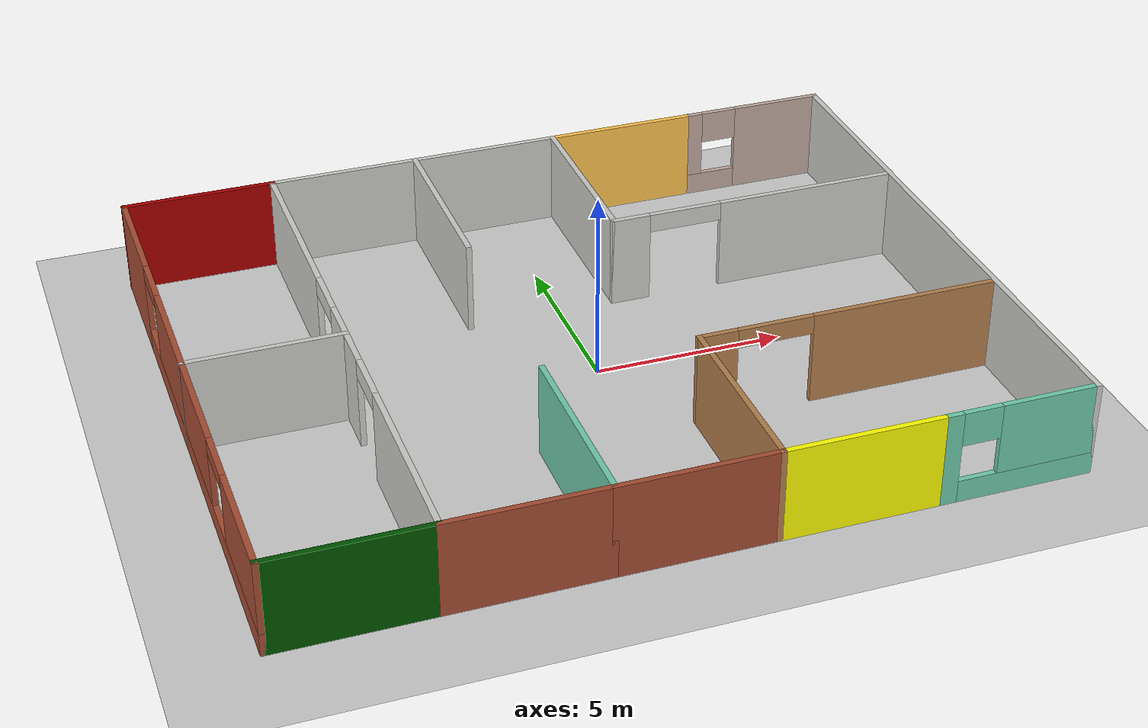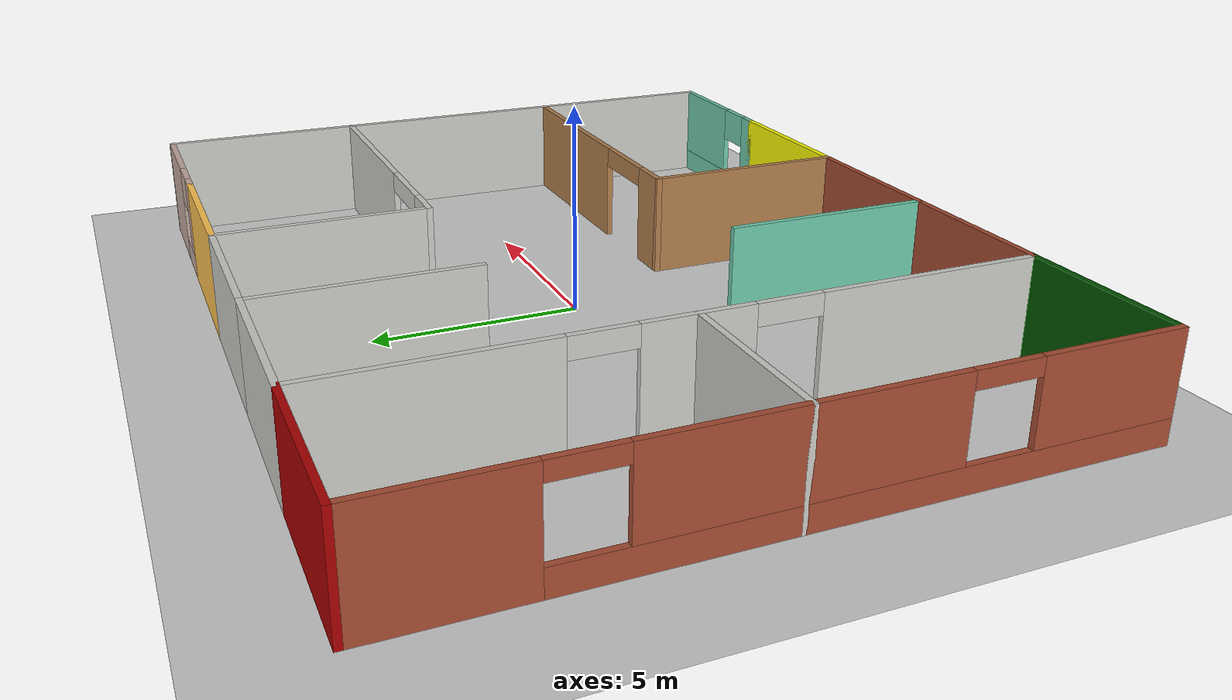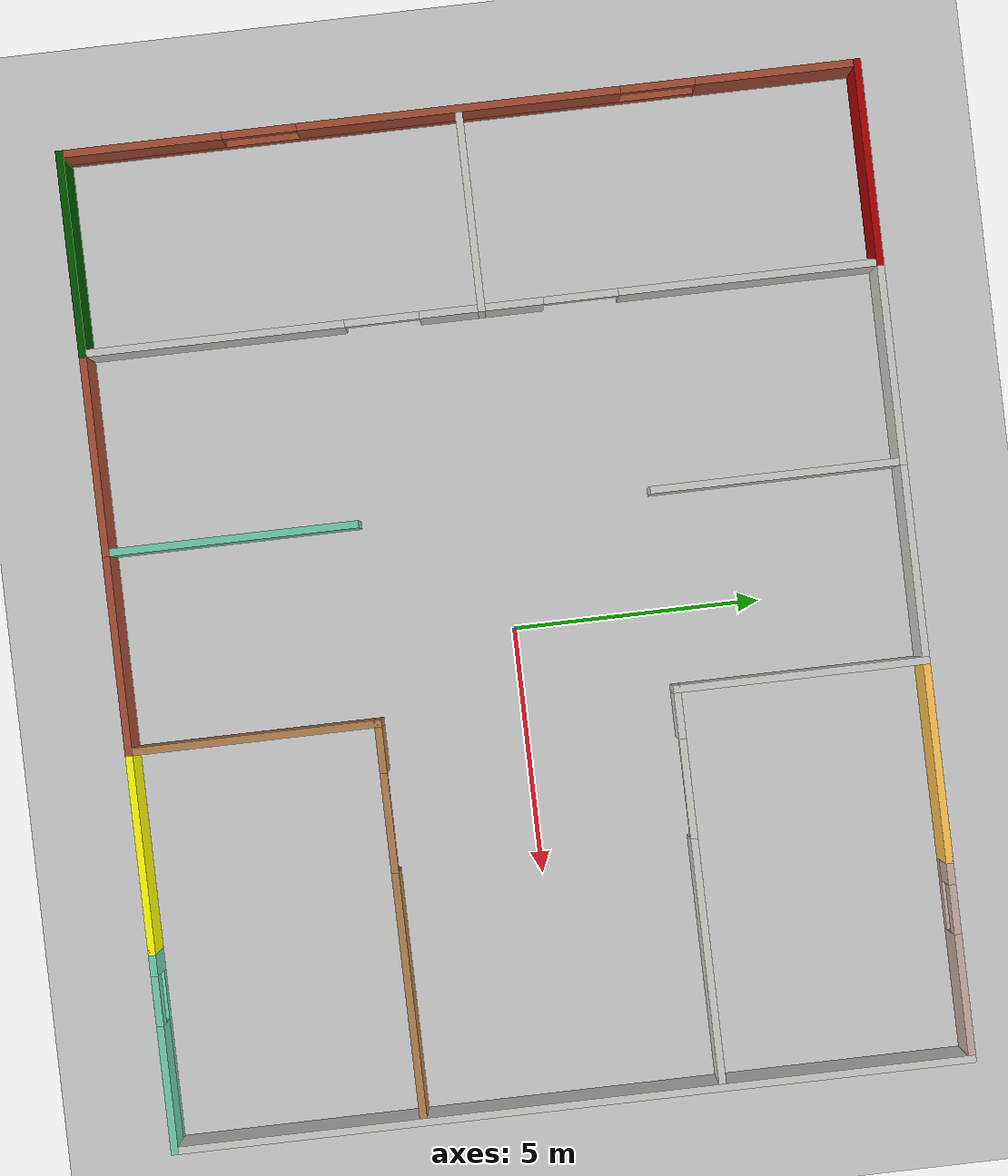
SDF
<sdf version="1.6">
 <world name="default">
  <model name="ground_plane">
   <static>1</static>
   <link name="link">
    <collision name="collision">
     <geometry><plane><normal>0 0 1</normal><size>100 100</size></plane></geometry>
     <surface>
      <contact><collide_bitmask>65535</collide_bitmask></contact>
      <friction><ode><mu>100</mu><mu2>50</mu2></ode></friction>
     </surface>
    </collision>
    <visual name="visual">
     <cast_shadows>0</cast_shadows>
     <geometry><plane><normal>0 0 1</normal><size>100 100</size></plane></geometry>
     <material>
      <script><uri>file://media/materials/scripts/gazebo.material</uri><name>Gazebo/Grey</name></script>
     </material>
    </visual>
   </link>
  </model>
  <light name="sun" type="directional">
   <pose>0 0 10 0 -0 0</pose>
   <diffuse>0.8 0.8 0.8 1</diffuse>
   <specular>0.2 0.2 0.2 1</specular>
   <attenuation>
    <range>1000</range>
    <constant>0.9</constant>
    <linear>0.01</linear>
    <quadratic>0.001</quadratic>
   </attenuation>
   <direction>-0.5 0.1 -0.9</direction>
  </light>
  <gravity>0 0 -9.8</gravity>
  <magnetic_field>6e-06 2.3e-05 -4.2e-05</magnetic_field>
  <atmosphere type="adiabatic"/>
  <physics name="default_physics" default="0" type="ode">
   <max_step_size>0.001</max_step_size>
   <real_time_factor>1</real_time_factor>
   <real_time_update_rate>1000</real_time_update_rate>
  </physics>
  <scene><ambient>0.4 0.4 0.4 1</ambient><background>0.7 0.7 0.7 1</background><shadows>1</shadows></scene>
  <spherical_coordinates>
   <surface_model>EARTH_WGS84</surface_model>
   <latitude_deg>0</latitude_deg>
   <longitude_deg>0</longitude_deg>
   <elevation>0</elevation>
   <heading_deg>0</heading_deg>
  </spherical_coordinates>
  <model name="Project_building">
   <link name="Wall_0">
    <pose>-8 8 0 0 -0 3.14159</pose>
    <visual name="Wall_0_Visual">
     <pose>0 0 1.25 0 -0 0</pose>
     <geometry><box><size>4.15 0.15 2.5</size></box></geometry>
     <material>
      <script><uri>file://media/materials/scripts/gazebo.material</uri><name>Gazebo/Grey</name></script>
      <ambient>0.666667 0 0 1</ambient>
      <shader type="pixel"/>
      <diffuse>0.7 0.7 0.7 1</diffuse>
      <specular>0.01 0.01 0.01 1</specular>
      <emissive>0 0 0 1</emissive>
     </material>
     <meta><layer>0</layer></meta>
    </visual>
    <collision name="Wall_0_Collision">
     <pose>0 0 1.25 0 -0 0</pose>
     <geometry><box><size>4.15 0.15 2.5</size></box></geometry>
     <surface>
      <friction>
       <ode><mu>1</mu><mu2>1</mu2><fdir1>0 0 0</fdir1><slip1>0</slip1><slip2>0</slip2></ode>
       <torsional>
        <coefficient>1</coefficient>
        <patch_radius>0</patch_radius>
        <surface_radius>0</surface_radius>
        <use_patch_radius>1</use_patch_radius>
        <ode><slip>0</slip></ode>
       </torsional>
      </friction>
      <bounce><restitution_coefficient>0</restitution_coefficient><threshold>1e+06</threshold></bounce>
      <contact>
       <collide_without_contact>0</collide_without_contact>
       <collide_without_contact_bitmask>1</collide_without_contact_bitmask>
       <collide_bitmask>1</collide_bitmask>
       <ode>
        <soft_cfm>0</soft_cfm>
        <soft_erp>0.2</soft_erp>
        <kp>1e+13</kp>
        <kd>1</kd>
        <max_vel>0.01</max_vel>
        <min_depth>0</min_depth>
       </ode>
       <bullet>
        <split_impulse>1</split_impulse>
        <split_impulse_penetration_threshold>-0.01</split_impulse_penetration_threshold>
        <soft_cfm>0</soft_cfm>
        <soft_erp>0.2</soft_erp>
        <kp>1e+13</kp>
        <kd>1</kd>
       </bullet>
      </contact>
     </surface>
    </collision>
   </link>
   <link name="Wall_10">
    <pose>-8 -8 0 0 -0 0</pose>
    <visual name="Wall_10_Visual">
     <pose>0 0 1.25 0 -0 0</pose>
     <geometry><box><size>4.15 0.15 2.5</size></box></geometry>
     <material>
      <script><uri>file://media/materials/scripts/gazebo.material</uri><name>Gazebo/Grey</name></script>
      <ambient>0 0.333333 0 1</ambient>
      <shader type="pixel"/>
      <diffuse>0.7 0.7 0.7 1</diffuse>
      <specular>0.01 0.01 0.01 1</specular>
      <emissive>0 0 0 1</emissive>
     </material>
     <meta><layer>0</layer></meta>
    </visual>
    <collision name="Wall_10_Collision">
     <pose>0 0 1.25 0 -0 0</pose>
     <geometry><box><size>4.15 0.15 2.5</size></box></geometry>
     <surface>
      <friction>
       <ode><mu>1</mu><mu2>1</mu2><fdir1>0 0 0</fdir1><slip1>0</slip1><slip2>0</slip2></ode>
       <torsional>
        <coefficient>1</coefficient>
        <patch_radius>0</patch_radius>
        <surface_radius>0</surface_radius>
        <use_patch_radius>1</use_patch_radius>
        <ode><slip>0</slip></ode>
       </torsional>
      </friction>
      <bounce><restitution_coefficient>0</restitution_coefficient><threshold>1e+06</threshold></bounce>
      <contact>
       <collide_without_contact>0</collide_without_contact>
       <collide_without_contact_bitmask>1</collide_without_contact_bitmask>
       <collide_bitmask>1</collide_bitmask>
       <ode>
        <soft_cfm>0</soft_cfm>
        <soft_erp>0.2</soft_erp>
        <kp>1e+13</kp>
        <kd>1</kd>
        <max_vel>0.01</max_vel>
        <min_depth>0</min_depth>
       </ode>
       <bullet>
        <split_impulse>1</split_impulse>
        <split_impulse_penetration_threshold>-0.01</split_impulse_penetration_threshold>
        <soft_cfm>0</soft_cfm>
        <soft_erp>0.2</soft_erp>
        <kp>1e+13</kp>
        <kd>1</kd>
       </bullet>
      </contact>
     </surface>
    </collision>
   </link>
   <link name="Wall_12">
    <pose>-4 -8 0 0 -0 0</pose>
    <visual name="Wall_12_Visual">
     <pose>0 0 1.25 0 -0 0</pose>
     <geometry><box><size>4.15 0.15 2.5</size></box></geometry>
     <material>
      <script><uri>file://media/materials/scripts/gazebo.material</uri><name>Gazebo/Bricks</name></script>
      <ambient>0.333333 0 0 1</ambient>
      <shader type="pixel"/>
      <diffuse>1 1 1 1</diffuse>
      <specular>0.2 0.2 0.2 1</specular>
      <emissive>0 0 0 1</emissive>
     </material>
     <meta><layer>0</layer></meta>
    </visual>
    <collision name="Wall_12_Collision">
     <pose>0 0 1.25 0 -0 0</pose>
     <geometry><box><size>4.15 0.15 2.5</size></box></geometry>
     <surface>
      <friction>
       <ode><mu>1</mu><mu2>1</mu2><fdir1>0 0 0</fdir1><slip1>0</slip1><slip2>0</slip2></ode>
       <torsional>
        <coefficient>1</coefficient>
        <patch_radius>0</patch_radius>
        <surface_radius>0</surface_radius>
        <use_patch_radius>1</use_patch_radius>
        <ode><slip>0</slip></ode>
       </torsional>
      </friction>
      <bounce><restitution_coefficient>0</restitution_coefficient><threshold>1e+06</threshold></bounce>
      <contact>
       <collide_without_contact>0</collide_without_contact>
       <collide_without_contact_bitmask>1</collide_without_contact_bitmask>
       <collide_bitmask>1</collide_bitmask>
       <ode>
        <soft_cfm>0</soft_cfm>
        <soft_erp>0.2</soft_erp>
        <kp>1e+13</kp>
        <kd>1</kd>
        <max_vel>0.01</max_vel>
        <min_depth>0</min_depth>
       </ode>
       <bullet>
        <split_impulse>1</split_impulse>
        <split_impulse_penetration_threshold>-0.01</split_impulse_penetration_threshold>
        <soft_cfm>0</soft_cfm>
        <soft_erp>0.2</soft_erp>
        <kp>1e+13</kp>
        <kd>1</kd>
       </bullet>
      </contact>
     </surface>
    </collision>
   </link>
   <link name="Wall_14">
    <pose>0 -8 0 0 -0 0</pose>
    <visual name="Wall_14_Visual">
     <pose>0 0 1.25 0 -0 0</pose>
     <geometry><box><size>4.15 0.15 2.5</size></box></geometry>
     <material>
      <script><uri>file://media/materials/scripts/gazebo.material</uri><name>Gazebo/Bricks</name></script>
      <ambient>1 1 1 1</ambient>
      <shader type="pixel"/>
      <diffuse>1 1 1 1</diffuse>
      <specular>0.2 0.2 0.2 1</specular>
      <emissive>0 0 0 1</emissive>
     </material>
     <meta><layer>0</layer></meta>
    </visual>
    <collision name="Wall_14_Collision">
     <pose>0 0 1.25 0 -0 0</pose>
     <geometry><box><size>4.15 0.15 2.5</size></box></geometry>
     <surface>
      <friction>
       <ode><mu>1</mu><mu2>1</mu2><fdir1>0 0 0</fdir1><slip1>0</slip1><slip2>0</slip2></ode>
       <torsional>
        <coefficient>1</coefficient>
        <patch_radius>0</patch_radius>
        <surface_radius>0</surface_radius>
        <use_patch_radius>1</use_patch_radius>
        <ode><slip>0</slip></ode>
       </torsional>
      </friction>
      <bounce><restitution_coefficient>0</restitution_coefficient><threshold>1e+06</threshold></bounce>
      <contact>
       <collide_without_contact>0</collide_without_contact>
       <collide_without_contact_bitmask>1</collide_without_contact_bitmask>
       <collide_bitmask>1</collide_bitmask>
       <ode>
        <soft_cfm>0</soft_cfm>
        <soft_erp>0.2</soft_erp>
        <kp>1e+13</kp>
        <kd>1</kd>
        <max_vel>0.01</max_vel>
        <min_depth>0</min_depth>
       </ode>
       <bullet>
        <split_impulse>1</split_impulse>
        <split_impulse_penetration_threshold>-0.01</split_impulse_penetration_threshold>
        <soft_cfm>0</soft_cfm>
        <soft_erp>0.2</soft_erp>
        <kp>1e+13</kp>
        <kd>1</kd>
       </bullet>
      </contact>
     </surface>
    </collision>
   </link>
   <link name="Wall_16">
    <pose>4 -8 0 0 -0 0</pose>
    <visual name="Wall_16_Visual">
     <pose>0 0 1.25 0 -0 0</pose>
     <geometry><box><size>4.15 0.15 2.5</size></box></geometry>
     <material>
      <script><uri>file://media/materials/scripts/gazebo.material</uri><name>Gazebo/Grey</name></script>
      <ambient>1 1 0 1</ambient>
      <shader type="pixel"/>
      <diffuse>0.7 0.7 0.7 1</diffuse>
      <specular>0.01 0.01 0.01 1</specular>
      <emissive>0 0 0 1</emissive>
     </material>
     <meta><layer>0</layer></meta>
    </visual>
    <collision name="Wall_16_Collision">
     <pose>0 0 1.25 0 -0 0</pose>
     <geometry><box><size>4.15 0.15 2.5</size></box></geometry>
     <surface>
      <friction>
       <ode><mu>1</mu><mu2>1</mu2><fdir1>0 0 0</fdir1><slip1>0</slip1><slip2>0</slip2></ode>
       <torsional>
        <coefficient>1</coefficient>
        <patch_radius>0</patch_radius>
        <surface_radius>0</surface_radius>
        <use_patch_radius>1</use_patch_radius>
        <ode><slip>0</slip></ode>
       </torsional>
      </friction>
      <bounce><restitution_coefficient>0</restitution_coefficient><threshold>1e+06</threshold></bounce>
      <contact>
       <collide_without_contact>0</collide_without_contact>
       <collide_without_contact_bitmask>1</collide_without_contact_bitmask>
       <collide_bitmask>1</collide_bitmask>
       <ode>
        <soft_cfm>0</soft_cfm>
        <soft_erp>0.2</soft_erp>
        <kp>1e+13</kp>
        <kd>1</kd>
        <max_vel>0.01</max_vel>
        <min_depth>0</min_depth>
       </ode>
       <bullet>
        <split_impulse>1</split_impulse>
        <split_impulse_penetration_threshold>-0.01</split_impulse_penetration_threshold>
        <soft_cfm>0</soft_cfm>
        <soft_erp>0.2</soft_erp>
        <kp>1e+13</kp>
        <kd>1</kd>
       </bullet>
      </contact>
     </surface>
    </collision>
   </link>
   <link name="Wall_18">
    <pose>8 -8 0 0 -0 0</pose>
    <visual name="Wall_18_Visual_0">
     <pose>-1.7875 0 1.25 0 -0 0</pose>
     <geometry><box><size>0.575 0.15 2.5</size></box></geometry>
     <material>
      <script><uri>file://media/materials/scripts/gazebo.material</uri><name>Gazebo/Grey</name></script>
      <ambient>0.435294 0.796078 0.67451 1</ambient>
      <shader type="pixel"/>
      <diffuse>0.7 0.7 0.7 1</diffuse>
      <specular>0.01 0.01 0.01 1</specular>
      <emissive>0 0 0 1</emissive>
     </material>
     <meta><layer>0</layer></meta>
    </visual>
    <visual name="Wall_18_Visual_1">
     <pose>0.2875 0 0.3 0 -0 0</pose>
     <geometry><box><size>3.575 0.15 0.6</size></box></geometry>
     <material>
      <script><uri>file://media/materials/scripts/gazebo.material</uri><name>Gazebo/Grey</name></script>
      <ambient>0.435294 0.796078 0.67451 1</ambient>
      <shader type="pixel"/>
      <diffuse>0.7 0.7 0.7 1</diffuse>
      <specular>0.01 0.01 0.01 1</specular>
      <emissive>0 0 0 1</emissive>
     </material>
     <meta><layer>0</layer></meta>
    </visual>
    <visual name="Wall_18_Visual_2">
     <pose>0.7875 0 1.55 0 -0 0</pose>
     <geometry><box><size>2.575 0.15 1.9</size></box></geometry>
     <material>
      <script><uri>file://media/materials/scripts/gazebo.material</uri><name>Gazebo/Grey</name></script>
      <ambient>0.435294 0.796078 0.67451 1</ambient>
      <shader type="pixel"/>
      <diffuse>0.7 0.7 0.7 1</diffuse>
      <specular>0.01 0.01 0.01 1</specular>
      <emissive>0 0 0 1</emissive>
     </material>
     <meta><layer>0</layer></meta>
    </visual>
    <visual name="Wall_18_Visual_3">
     <pose>-1 0 2.05 0 -0 0</pose>
     <geometry><box><size>1 0.15 0.9</size></box></geometry>
     <material>
      <script><uri>file://media/materials/scripts/gazebo.material</uri><name>Gazebo/Grey</name></script>
      <ambient>0.435294 0.796078 0.67451 1</ambient>
      <shader type="pixel"/>
      <diffuse>0.7 0.7 0.7 1</diffuse>
      <specular>0.01 0.01 0.01 1</specular>
      <emissive>0 0 0 1</emissive>
     </material>
     <meta><layer>0</layer></meta>
    </visual>
    <collision name="Wall_18_Collision_0">
     <pose>-1.7875 0 1.25 0 -0 0</pose>
     <geometry><box><size>0.575 0.15 2.5</size></box></geometry>
     <surface>
      <friction>
       <ode><mu>1</mu><mu2>1</mu2><fdir1>0 0 0</fdir1><slip1>0</slip1><slip2>0</slip2></ode>
       <torsional>
        <coefficient>1</coefficient>
        <patch_radius>0</patch_radius>
        <surface_radius>0</surface_radius>
        <use_patch_radius>1</use_patch_radius>
        <ode><slip>0</slip></ode>
       </torsional>
      </friction>
      <bounce><restitution_coefficient>0</restitution_coefficient><threshold>1e+06</threshold></bounce>
      <contact>
       <collide_without_contact>0</collide_without_contact>
       <collide_without_contact_bitmask>1</collide_without_contact_bitmask>
       <collide_bitmask>1</collide_bitmask>
       <ode>
        <soft_cfm>0</soft_cfm>
        <soft_erp>0.2</soft_erp>
        <kp>1e+13</kp>
        <kd>1</kd>
        <max_vel>0.01</max_vel>
        <min_depth>0</min_depth>
       </ode>
       <bullet>
        <split_impulse>1</split_impulse>
        <split_impulse_penetration_threshold>-0.01</split_impulse_penetration_threshold>
        <soft_cfm>0</soft_cfm>
        <soft_erp>0.2</soft_erp>
        <kp>1e+13</kp>
        <kd>1</kd>
       </bullet>
      </contact>
     </surface>
    </collision>
    <collision name="Wall_18_Collision_1">
     <pose>0.2875 0 0.3 0 -0 0</pose>
     <geometry><box><size>3.575 0.15 0.6</size></box></geometry>
     <surface>
      <friction>
       <ode><mu>1</mu><mu2>1</mu2><fdir1>0 0 0</fdir1><slip1>0</slip1><slip2>0</slip2></ode>
       <torsional>
        <coefficient>1</coefficient>
        <patch_radius>0</patch_radius>
        <surface_radius>0</surface_radius>
        <use_patch_radius>1</use_patch_radius>
        <ode><slip>0</slip></ode>
       </torsional>
      </friction>
      <bounce><restitution_coefficient>0</restitution_coefficient><threshold>1e+06</threshold></bounce>
      <contact>
       <collide_without_contact>0</collide_without_contact>
       <collide_without_contact_bitmask>1</collide_without_contact_bitmask>
       <collide_bitmask>1</collide_bitmask>
       <ode>
        <soft_cfm>0</soft_cfm>
        <soft_erp>0.2</soft_erp>
        <kp>1e+13</kp>
        <kd>1</kd>
        <max_vel>0.01</max_vel>
        <min_depth>0</min_depth>
       </ode>
       <bullet>
        <split_impulse>1</split_impulse>
        <split_impulse_penetration_threshold>-0.01</split_impulse_penetration_threshold>
        <soft_cfm>0</soft_cfm>
        <soft_erp>0.2</soft_erp>
        <kp>1e+13</kp>
        <kd>1</kd>
       </bullet>
      </contact>
     </surface>
    </collision>
    <collision name="Wall_18_Collision_2">
     <pose>0.7875 0 1.55 0 -0 0</pose>
     <geometry><box><size>2.575 0.15 1.9</size></box></geometry>
     <surface>
      <friction>
       <ode><mu>1</mu><mu2>1</mu2><fdir1>0 0 0</fdir1><slip1>0</slip1><slip2>0</slip2></ode>
       <torsional>
        <coefficient>1</coefficient>
        <patch_radius>0</patch_radius>
        <surface_radius>0</surface_radius>
        <use_patch_radius>1</use_patch_radius>
        <ode><slip>0</slip></ode>
       </torsional>
      </friction>
      <bounce><restitution_coefficient>0</restitution_coefficient><threshold>1e+06</threshold></bounce>
      <contact>
       <collide_without_contact>0</collide_without_contact>
       <collide_without_contact_bitmask>1</collide_without_contact_bitmask>
       <collide_bitmask>1</collide_bitmask>
       <ode>
        <soft_cfm>0</soft_cfm>
        <soft_erp>0.2</soft_erp>
        <kp>1e+13</kp>
        <kd>1</kd>
        <max_vel>0.01</max_vel>
        <min_depth>0</min_depth>
       </ode>
       <bullet>
        <split_impulse>1</split_impulse>
        <split_impulse_penetration_threshold>-0.01</split_impulse_penetration_threshold>
        <soft_cfm>0</soft_cfm>
        <soft_erp>0.2</soft_erp>
        <kp>1e+13</kp>
        <kd>1</kd>
       </bullet>
      </contact>
     </surface>
    </collision>
    <collision name="Wall_18_Collision_3">
     <pose>-1 0 2.05 0 -0 0</pose>
     <geometry><box><size>1 0.15 0.9</size></box></geometry>
     <surface>
      <friction>
       <ode><mu>1</mu><mu2>1</mu2><fdir1>0 0 0</fdir1><slip1>0</slip1><slip2>0</slip2></ode>
       <torsional>
        <coefficient>1</coefficient>
        <patch_radius>0</patch_radius>
        <surface_radius>0</surface_radius>
        <use_patch_radius>1</use_patch_radius>
        <ode><slip>0</slip></ode>
       </torsional>
      </friction>
      <bounce><restitution_coefficient>0</restitution_coefficient><threshold>1e+06</threshold></bounce>
      <contact>
       <collide_without_contact>0</collide_without_contact>
       <collide_without_contact_bitmask>1</collide_without_contact_bitmask>
       <collide_bitmask>1</collide_bitmask>
       <ode>
        <soft_cfm>0</soft_cfm>
        <soft_erp>0.2</soft_erp>
        <kp>1e+13</kp>
        <kd>1</kd>
        <max_vel>0.01</max_vel>
        <min_depth>0</min_depth>
       </ode>
       <bullet>
        <split_impulse>1</split_impulse>
        <split_impulse_penetration_threshold>-0.01</split_impulse_penetration_threshold>
        <soft_cfm>0</soft_cfm>
        <soft_erp>0.2</soft_erp>
        <kp>1e+13</kp>
        <kd>1</kd>
       </bullet>
      </contact>
     </surface>
    </collision>
   </link>
   <link name="Wall_2">
    <pose>-4 8 0 0 -0 3.14159</pose>
    <visual name="Wall_2_Visual">
     <pose>0 0 1.25 0 -0 0</pose>
     <geometry><box><size>4.15 0.15 2.5</size></box></geometry>
     <material>
      <script><uri>file://media/materials/scripts/gazebo.material</uri><name>Gazebo/CeilingTiled</name></script>
      <ambient>0 0 0.498039 1</ambient>
      <shader type="pixel"/>
      <diffuse>1 1 1 1</diffuse>
      <specular>0 0 0 1</specular>
      <emissive>0 0 0 1</emissive>
     </material>
     <meta><layer>0</layer></meta>
    </visual>
    <collision name="Wall_2_Collision">
     <pose>0 0 1.25 0 -0 0</pose>
     <geometry><box><size>4.15 0.15 2.5</size></box></geometry>
     <surface>
      <friction>
       <ode><mu>1</mu><mu2>1</mu2><fdir1>0 0 0</fdir1><slip1>0</slip1><slip2>0</slip2></ode>
       <torsional>
        <coefficient>1</coefficient>
        <patch_radius>0</patch_radius>
        <surface_radius>0</surface_radius>
        <use_patch_radius>1</use_patch_radius>
        <ode><slip>0</slip></ode>
       </torsional>
      </friction>
      <bounce><restitution_coefficient>0</restitution_coefficient><threshold>1e+06</threshold></bounce>
      <contact>
       <collide_without_contact>0</collide_without_contact>
       <collide_without_contact_bitmask>1</collide_without_contact_bitmask>
       <collide_bitmask>1</collide_bitmask>
       <ode>
        <soft_cfm>0</soft_cfm>
        <soft_erp>0.2</soft_erp>
        <kp>1e+13</kp>
        <kd>1</kd>
        <max_vel>0.01</max_vel>
        <min_depth>0</min_depth>
       </ode>
       <bullet>
        <split_impulse>1</split_impulse>
        <split_impulse_penetration_threshold>-0.01</split_impulse_penetration_threshold>
        <soft_cfm>0</soft_cfm>
        <soft_erp>0.2</soft_erp>
        <kp>1e+13</kp>
        <kd>1</kd>
       </bullet>
      </contact>
     </surface>
    </collision>
   </link>
   <link name="Wall_20">
    <pose>10 0 0 0 0 -1.5708</pose>
    <visual name="Wall_20_Visual">
     <pose>0 0 1.25 0 -0 0</pose>
     <geometry><box><size>16.15 0.15 2.5</size></box></geometry>
     <material>
      <script><uri>file://media/materials/scripts/gazebo.material</uri><name>Gazebo/CeilingTiled</name></script>
      <ambient>1 0.333333 0 1</ambient>
      <shader type="pixel"/>
      <diffuse>1 1 1 1</diffuse>
      <specular>0 0 0 1</specular>
      <emissive>0 0 0 1</emissive>
     </material>
     <meta><layer>0</layer></meta>
    </visual>
    <collision name="Wall_20_Collision">
     <pose>0 0 1.25 0 -0 0</pose>
     <geometry><box><size>16.15 0.15 2.5</size></box></geometry>
     <surface>
      <friction>
       <ode><mu>1</mu><mu2>1</mu2><fdir1>0 0 0</fdir1><slip1>0</slip1><slip2>0</slip2></ode>
       <torsional>
        <coefficient>1</coefficient>
        <patch_radius>0</patch_radius>
        <surface_radius>0</surface_radius>
        <use_patch_radius>1</use_patch_radius>
        <ode><slip>0</slip></ode>
       </torsional>
      </friction>
      <bounce><restitution_coefficient>0</restitution_coefficient><threshold>1e+06</threshold></bounce>
      <contact>
       <collide_without_contact>0</collide_without_contact>
       <collide_without_contact_bitmask>1</collide_without_contact_bitmask>
       <collide_bitmask>1</collide_bitmask>
       <ode>
        <soft_cfm>0</soft_cfm>
        <soft_erp>0.2</soft_erp>
        <kp>1e+13</kp>
        <kd>1</kd>
        <max_vel>0.01</max_vel>
        <min_depth>0</min_depth>
       </ode>
       <bullet>
        <split_impulse>1</split_impulse>
        <split_impulse_penetration_threshold>-0.01</split_impulse_penetration_threshold>
        <soft_cfm>0</soft_cfm>
        <soft_erp>0.2</soft_erp>
        <kp>1e+13</kp>
        <kd>1</kd>
       </bullet>
      </contact>
     </surface>
    </collision>
   </link>
   <link name="Wall_22">
    <pose>-10 0 0 0 0 -1.5708</pose>
    <visual name="Wall_22_Visual_0">
     <pose>-6.4125 0 1.25 0 -0 0</pose>
     <geometry><box><size>3.325 0.15 2.5</size></box></geometry>
     <material>
      <script><uri>file://media/materials/scripts/gazebo.material</uri><name>Gazebo/Bricks</name></script>
      <ambient>1 1 1 1</ambient>
      <shader type="pixel"/>
      <diffuse>1 1 1 1</diffuse>
      <specular>0.2 0.2 0.2 1</specular>
      <emissive>0 0 0 1</emissive>
     </material>
     <meta><layer>0</layer></meta>
    </visual>
    <visual name="Wall_22_Visual_1">
     <pose>1.6625 0 0.3 0 -0 0</pose>
     <geometry><box><size>12.825 0.15 0.6</size></box></geometry>
     <material>
      <script><uri>file://media/materials/scripts/gazebo.material</uri><name>Gazebo/Bricks</name></script>
      <ambient>1 1 1 1</ambient>
      <shader type="pixel"/>
      <diffuse>1 1 1 1</diffuse>
      <specular>0.2 0.2 0.2 1</specular>
      <emissive>0 0 0 1</emissive>
     </material>
     <meta><layer>0</layer></meta>
    </visual>
    <visual name="Wall_22_Visual_2">
     <pose>0 0 1.55 0 -0 0</pose>
     <geometry><box><size>6.5 0.15 1.9</size></box></geometry>
     <material>
      <script><uri>file://media/materials/scripts/gazebo.material</uri><name>Gazebo/Bricks</name></script>
      <ambient>1 1 1 1</ambient>
      <shader type="pixel"/>
      <diffuse>1 1 1 1</diffuse>
      <specular>0.2 0.2 0.2 1</specular>
      <emissive>0 0 0 1</emissive>
     </material>
     <meta><layer>0</layer></meta>
    </visual>
    <visual name="Wall_22_Visual_3">
     <pose>6.4125 0 1.55 0 -0 0</pose>
     <geometry><box><size>3.325 0.15 1.9</size></box></geometry>
     <material>
      <script><uri>file://media/materials/scripts/gazebo.material</uri><name>Gazebo/Bricks</name></script>
      <ambient>1 1 1 1</ambient>
      <shader type="pixel"/>
      <diffuse>1 1 1 1</diffuse>
      <specular>0.2 0.2 0.2 1</specular>
      <emissive>0 0 0 1</emissive>
     </material>
     <meta><layer>0</layer></meta>
    </visual>
    <visual name="Wall_22_Visual_4">
     <pose>-4 0 2.3 0 -0 0</pose>
     <geometry><box><size>1.5 0.15 0.4</size></box></geometry>
     <material>
      <script><uri>file://media/materials/scripts/gazebo.material</uri><name>Gazebo/Bricks</name></script>
      <ambient>1 1 1 1</ambient>
      <shader type="pixel"/>
      <diffuse>1 1 1 1</diffuse>
      <specular>0.2 0.2 0.2 1</specular>
      <emissive>0 0 0 1</emissive>
     </material>
     <meta><layer>0</layer></meta>
    </visual>
    <visual name="Wall_22_Visual_5">
     <pose>4 0 2.3 0 -0 0</pose>
     <geometry><box><size>1.5 0.15 0.4</size></box></geometry>
     <material>
      <script><uri>file://media/materials/scripts/gazebo.material</uri><name>Gazebo/Bricks</name></script>
      <ambient>1 1 1 1</ambient>
      <shader type="pixel"/>
      <diffuse>1 1 1 1</diffuse>
      <specular>0.2 0.2 0.2 1</specular>
      <emissive>0 0 0 1</emissive>
     </material>
     <meta><layer>0</layer></meta>
    </visual>
    <collision name="Wall_22_Collision_0">
     <pose>-6.4125 0 1.25 0 -0 0</pose>
     <geometry><box><size>3.325 0.15 2.5</size></box></geometry>
     <surface>
      <friction>
       <ode><mu>1</mu><mu2>1</mu2><fdir1>0 0 0</fdir1><slip1>0</slip1><slip2>0</slip2></ode>
       <torsional>
        <coefficient>1</coefficient>
        <patch_radius>0</patch_radius>
        <surface_radius>0</surface_radius>
        <use_patch_radius>1</use_patch_radius>
        <ode><slip>0</slip></ode>
       </torsional>
      </friction>
      <bounce><restitution_coefficient>0</restitution_coefficient><threshold>1e+06</threshold></bounce>
      <contact>
       <collide_without_contact>0</collide_without_contact>
       <collide_without_contact_bitmask>1</collide_without_contact_bitmask>
       <collide_bitmask>1</collide_bitmask>
       <ode>
        <soft_cfm>0</soft_cfm>
        <soft_erp>0.2</soft_erp>
        <kp>1e+13</kp>
        <kd>1</kd>
        <max_vel>0.01</max_vel>
        <min_depth>0</min_depth>
       </ode>
       <bullet>
        <split_impulse>1</split_impulse>
        <split_impulse_penetration_threshold>-0.01</split_impulse_penetration_threshold>
        <soft_cfm>0</soft_cfm>
        <soft_erp>0.2</soft_erp>
        <kp>1e+13</kp>
        <kd>1</kd>
       </bullet>
      </contact>
     </surface>
    </collision>
    <collision name="Wall_22_Collision_1">
     <pose>1.6625 0 0.3 0 -0 0</pose>
     <geometry><box><size>12.825 0.15 0.6</size></box></geometry>
     <surface>
      <friction>
       <ode><mu>1</mu><mu2>1</mu2><fdir1>0 0 0</fdir1><slip1>0</slip1><slip2>0</slip2></ode>
       <torsional>
        <coefficient>1</coefficient>
        <patch_radius>0</patch_radius>
        <surface_radius>0</surface_radius>
        <use_patch_radius>1</use_patch_radius>
        <ode><slip>0</slip></ode>
       </torsional>
      </friction>
      <bounce><restitution_coefficient>0</restitution_coefficient><threshold>1e+06</threshold></bounce>
      <contact>
       <collide_without_contact>0</collide_without_contact>
       <collide_without_contact_bitmask>1</collide_without_contact_bitmask>
       <collide_bitmask>1</collide_bitmask>
       <ode>
        <soft_cfm>0</soft_cfm>
        <soft_erp>0.2</soft_erp>
        <kp>1e+13</kp>
        <kd>1</kd>
        <max_vel>0.01</max_vel>
        <min_depth>0</min_depth>
       </ode>
       <bullet>
        <split_impulse>1</split_impulse>
        <split_impulse_penetration_threshold>-0.01</split_impulse_penetration_threshold>
        <soft_cfm>0</soft_cfm>
        <soft_erp>0.2</soft_erp>
        <kp>1e+13</kp>
        <kd>1</kd>
       </bullet>
      </contact>
     </surface>
    </collision>
    <collision name="Wall_22_Collision_2">
     <pose>0 0 1.55 0 -0 0</pose>
     <geometry><box><size>6.5 0.15 1.9</size></box></geometry>
     <surface>
      <friction>
       <ode><mu>1</mu><mu2>1</mu2><fdir1>0 0 0</fdir1><slip1>0</slip1><slip2>0</slip2></ode>
       <torsional>
        <coefficient>1</coefficient>
        <patch_radius>0</patch_radius>
        <surface_radius>0</surface_radius>
        <use_patch_radius>1</use_patch_radius>
        <ode><slip>0</slip></ode>
       </torsional>
      </friction>
      <bounce><restitution_coefficient>0</restitution_coefficient><threshold>1e+06</threshold></bounce>
      <contact>
       <collide_without_contact>0</collide_without_contact>
       <collide_without_contact_bitmask>1</collide_without_contact_bitmask>
       <collide_bitmask>1</collide_bitmask>
       <ode>
        <soft_cfm>0</soft_cfm>
        <soft_erp>0.2</soft_erp>
        <kp>1e+13</kp>
        <kd>1</kd>
        <max_vel>0.01</max_vel>
        <min_depth>0</min_depth>
       </ode>
       <bullet>
        <split_impulse>1</split_impulse>
        <split_impulse_penetration_threshold>-0.01</split_impulse_penetration_threshold>
        <soft_cfm>0</soft_cfm>
        <soft_erp>0.2</soft_erp>
        <kp>1e+13</kp>
        <kd>1</kd>
       </bullet>
      </contact>
     </surface>
    </collision>
    <collision name="Wall_22_Collision_3">
     <pose>6.4125 0 1.55 0 -0 0</pose>
     <geometry><box><size>3.325 0.15 1.9</size></box></geometry>
     <surface>
      <friction>
       <ode><mu>1</mu><mu2>1</mu2><fdir1>0 0 0</fdir1><slip1>0</slip1><slip2>0</slip2></ode>
       <torsional>
        <coefficient>1</coefficient>
        <patch_radius>0</patch_radius>
        <surface_radius>0</surface_radius>
        <use_patch_radius>1</use_patch_radius>
        <ode><slip>0</slip></ode>
       </torsional>
      </friction>
      <bounce><restitution_coefficient>0</restitution_coefficient><threshold>1e+06</threshold></bounce>
      <contact>
       <collide_without_contact>0</collide_without_contact>
       <collide_without_contact_bitmask>1</collide_without_contact_bitmask>
       <collide_bitmask>1</collide_bitmask>
       <ode>
        <soft_cfm>0</soft_cfm>
        <soft_erp>0.2</soft_erp>
        <kp>1e+13</kp>
        <kd>1</kd>
        <max_vel>0.01</max_vel>
        <min_depth>0</min_depth>
       </ode>
       <bullet>
        <split_impulse>1</split_impulse>
        <split_impulse_penetration_threshold>-0.01</split_impulse_penetration_threshold>
        <soft_cfm>0</soft_cfm>
        <soft_erp>0.2</soft_erp>
        <kp>1e+13</kp>
        <kd>1</kd>
       </bullet>
      </contact>
     </surface>
    </collision>
    <collision name="Wall_22_Collision_4">
     <pose>-4 0 2.3 0 -0 0</pose>
     <geometry><box><size>1.5 0.15 0.4</size></box></geometry>
     <surface>
      <friction>
       <ode><mu>1</mu><mu2>1</mu2><fdir1>0 0 0</fdir1><slip1>0</slip1><slip2>0</slip2></ode>
       <torsional>
        <coefficient>1</coefficient>
        <patch_radius>0</patch_radius>
        <surface_radius>0</surface_radius>
        <use_patch_radius>1</use_patch_radius>
        <ode><slip>0</slip></ode>
       </torsional>
      </friction>
      <bounce><restitution_coefficient>0</restitution_coefficient><threshold>1e+06</threshold></bounce>
      <contact>
       <collide_without_contact>0</collide_without_contact>
       <collide_without_contact_bitmask>1</collide_without_contact_bitmask>
       <collide_bitmask>1</collide_bitmask>
       <ode>
        <soft_cfm>0</soft_cfm>
        <soft_erp>0.2</soft_erp>
        <kp>1e+13</kp>
        <kd>1</kd>
        <max_vel>0.01</max_vel>
        <min_depth>0</min_depth>
       </ode>
       <bullet>
        <split_impulse>1</split_impulse>
        <split_impulse_penetration_threshold>-0.01</split_impulse_penetration_threshold>
        <soft_cfm>0</soft_cfm>
        <soft_erp>0.2</soft_erp>
        <kp>1e+13</kp>
        <kd>1</kd>
       </bullet>
      </contact>
     </surface>
    </collision>
    <collision name="Wall_22_Collision_5">
     <pose>4 0 2.3 0 -0 0</pose>
     <geometry><box><size>1.5 0.15 0.4</size></box></geometry>
     <surface>
      <friction>
       <ode><mu>1</mu><mu2>1</mu2><fdir1>0 0 0</fdir1><slip1>0</slip1><slip2>0</slip2></ode>
       <torsional>
        <coefficient>1</coefficient>
        <patch_radius>0</patch_radius>
        <surface_radius>0</surface_radius>
        <use_patch_radius>1</use_patch_radius>
        <ode><slip>0</slip></ode>
       </torsional>
      </friction>
      <bounce><restitution_coefficient>0</restitution_coefficient><threshold>1e+06</threshold></bounce>
      <contact>
       <collide_without_contact>0</collide_without_contact>
       <collide_without_contact_bitmask>1</collide_without_contact_bitmask>
       <collide_bitmask>1</collide_bitmask>
       <ode>
        <soft_cfm>0</soft_cfm>
        <soft_erp>0.2</soft_erp>
        <kp>1e+13</kp>
        <kd>1</kd>
        <max_vel>0.01</max_vel>
        <min_depth>0</min_depth>
       </ode>
       <bullet>
        <split_impulse>1</split_impulse>
        <split_impulse_penetration_threshold>-0.01</split_impulse_penetration_threshold>
        <soft_cfm>0</soft_cfm>
        <soft_erp>0.2</soft_erp>
        <kp>1e+13</kp>
        <kd>1</kd>
       </bullet>
      </contact>
     </surface>
    </collision>
   </link>
   <link name="Wall_24">
    <pose>-8 0 0 0 -0 0</pose>
    <visual name="Wall_24_Visual">
     <pose>0 0 1.25 0 -0 0</pose>
     <geometry><box><size>4.15 0.15 2.5</size></box></geometry>
     <material>
      <script><uri>file://media/materials/scripts/gazebo.material</uri><name>Gazebo/CeilingTiled</name></script>
      <ambient>0.996078 0.47451 0.0196078 1</ambient>
      <shader type="pixel"/>
      <diffuse>1 1 1 1</diffuse>
      <specular>0 0 0 1</specular>
      <emissive>0 0 0 1</emissive>
     </material>
     <meta><layer>0</layer></meta>
    </visual>
    <collision name="Wall_24_Collision">
     <pose>0 0 1.25 0 -0 0</pose>
     <geometry><box><size>4.15 0.15 2.5</size></box></geometry>
     <surface>
      <friction>
       <ode><mu>1</mu><mu2>1</mu2><fdir1>0 0 0</fdir1><slip1>0</slip1><slip2>0</slip2></ode>
       <torsional>
        <coefficient>1</coefficient>
        <patch_radius>0</patch_radius>
        <surface_radius>0</surface_radius>
        <use_patch_radius>1</use_patch_radius>
        <ode><slip>0</slip></ode>
       </torsional>
      </friction>
      <bounce><restitution_coefficient>0</restitution_coefficient><threshold>1e+06</threshold></bounce>
      <contact>
       <collide_without_contact>0</collide_without_contact>
       <collide_without_contact_bitmask>1</collide_without_contact_bitmask>
       <collide_bitmask>1</collide_bitmask>
       <ode>
        <soft_cfm>0</soft_cfm>
        <soft_erp>0.2</soft_erp>
        <kp>1e+13</kp>
        <kd>1</kd>
        <max_vel>0.01</max_vel>
        <min_depth>0</min_depth>
       </ode>
       <bullet>
        <split_impulse>1</split_impulse>
        <split_impulse_penetration_threshold>-0.01</split_impulse_penetration_threshold>
        <soft_cfm>0</soft_cfm>
        <soft_erp>0.2</soft_erp>
        <kp>1e+13</kp>
        <kd>1</kd>
       </bullet>
      </contact>
     </surface>
    </collision>
   </link>
   <link name="Wall_30">
    <pose>-6 0 0 0 0 -1.5708</pose>
    <visual name="Wall_30_Visual_0">
     <pose>-5.4125 0 1.25 0 -0 0</pose>
     <geometry><box><size>5.325 0.15 2.5</size></box></geometry>
     <material>
      <script><uri>file://media/materials/scripts/gazebo.material</uri><name>Gazebo/CeilingTiled</name></script>
      <ambient>0.921569 0.807843 0.615686 1</ambient>
      <shader type="pixel"/>
      <diffuse>1 1 1 1</diffuse>
      <specular>0 0 0 1</specular>
      <emissive>0 0 0 1</emissive>
     </material>
     <meta><layer>0</layer></meta>
    </visual>
    <visual name="Wall_30_Visual_1">
     <pose>0 0 1.25 0 -0 0</pose>
     <geometry><box><size>2.5 0.15 2.5</size></box></geometry>
     <material>
      <script><uri>file://media/materials/scripts/gazebo.material</uri><name>Gazebo/CeilingTiled</name></script>
      <ambient>0.921569 0.807843 0.615686 1</ambient>
      <shader type="pixel"/>
      <diffuse>1 1 1 1</diffuse>
      <specular>0 0 0 1</specular>
      <emissive>0 0 0 1</emissive>
     </material>
     <meta><layer>0</layer></meta>
    </visual>
    <visual name="Wall_30_Visual_2">
     <pose>5.4125 0 1.25 0 -0 0</pose>
     <geometry><box><size>5.325 0.15 2.5</size></box></geometry>
     <material>
      <script><uri>file://media/materials/scripts/gazebo.material</uri><name>Gazebo/CeilingTiled</name></script>
      <ambient>0.921569 0.807843 0.615686 1</ambient>
      <shader type="pixel"/>
      <diffuse>1 1 1 1</diffuse>
      <specular>0 0 0 1</specular>
      <emissive>0 0 0 1</emissive>
     </material>
     <meta><layer>0</layer></meta>
    </visual>
    <visual name="Wall_30_Visual_3">
     <pose>-2 0 2.25 0 -0 0</pose>
     <geometry><box><size>1.5 0.15 0.5</size></box></geometry>
     <material>
      <script><uri>file://media/materials/scripts/gazebo.material</uri><name>Gazebo/CeilingTiled</name></script>
      <ambient>0.921569 0.807843 0.615686 1</ambient>
      <shader type="pixel"/>
      <diffuse>1 1 1 1</diffuse>
      <specular>0 0 0 1</specular>
      <emissive>0 0 0 1</emissive>
     </material>
     <meta><layer>0</layer></meta>
    </visual>
    <visual name="Wall_30_Visual_4">
     <pose>2 0 2.25 0 -0 0</pose>
     <geometry><box><size>1.5 0.15 0.5</size></box></geometry>
     <material>
      <script><uri>file://media/materials/scripts/gazebo.material</uri><name>Gazebo/CeilingTiled</name></script>
      <ambient>0.921569 0.807843 0.615686 1</ambient>
      <shader type="pixel"/>
      <diffuse>1 1 1 1</diffuse>
      <specular>0 0 0 1</specular>
      <emissive>0 0 0 1</emissive>
     </material>
     <meta><layer>0</layer></meta>
    </visual>
    <collision name="Wall_30_Collision_0">
     <pose>-5.4125 0 1.25 0 -0 0</pose>
     <geometry><box><size>5.325 0.15 2.5</size></box></geometry>
     <surface>
      <friction>
       <ode><mu>1</mu><mu2>1</mu2><fdir1>0 0 0</fdir1><slip1>0</slip1><slip2>0</slip2></ode>
       <torsional>
        <coefficient>1</coefficient>
        <patch_radius>0</patch_radius>
        <surface_radius>0</surface_radius>
        <use_patch_radius>1</use_patch_radius>
        <ode><slip>0</slip></ode>
       </torsional>
      </friction>
      <bounce><restitution_coefficient>0</restitution_coefficient><threshold>1e+06</threshold></bounce>
      <contact>
       <collide_without_contact>0</collide_without_contact>
       <collide_without_contact_bitmask>1</collide_without_contact_bitmask>
       <collide_bitmask>1</collide_bitmask>
       <ode>
        <soft_cfm>0</soft_cfm>
        <soft_erp>0.2</soft_erp>
        <kp>1e+13</kp>
        <kd>1</kd>
        <max_vel>0.01</max_vel>
        <min_depth>0</min_depth>
       </ode>
       <bullet>
        <split_impulse>1</split_impulse>
        <split_impulse_penetration_threshold>-0.01</split_impulse_penetration_threshold>
        <soft_cfm>0</soft_cfm>
        <soft_erp>0.2</soft_erp>
        <kp>1e+13</kp>
        <kd>1</kd>
       </bullet>
      </contact>
     </surface>
    </collision>
    <collision name="Wall_30_Collision_1">
     <pose>0 0 1.25 0 -0 0</pose>
     <geometry><box><size>2.5 0.15 2.5</size></box></geometry>
     <surface>
      <friction>
       <ode><mu>1</mu><mu2>1</mu2><fdir1>0 0 0</fdir1><slip1>0</slip1><slip2>0</slip2></ode>
       <torsional>
        <coefficient>1</coefficient>
        <patch_radius>0</patch_radius>
        <surface_radius>0</surface_radius>
        <use_patch_radius>1</use_patch_radius>
        <ode><slip>0</slip></ode>
       </torsional>
      </friction>
      <bounce><restitution_coefficient>0</restitution_coefficient><threshold>1e+06</threshold></bounce>
      <contact>
       <collide_without_contact>0</collide_without_contact>
       <collide_without_contact_bitmask>1</collide_without_contact_bitmask>
       <collide_bitmask>1</collide_bitmask>
       <ode>
        <soft_cfm>0</soft_cfm>
        <soft_erp>0.2</soft_erp>
        <kp>1e+13</kp>
        <kd>1</kd>
        <max_vel>0.01</max_vel>
        <min_depth>0</min_depth>
       </ode>
       <bullet>
        <split_impulse>1</split_impulse>
        <split_impulse_penetration_threshold>-0.01</split_impulse_penetration_threshold>
        <soft_cfm>0</soft_cfm>
        <soft_erp>0.2</soft_erp>
        <kp>1e+13</kp>
        <kd>1</kd>
       </bullet>
      </contact>
     </surface>
    </collision>
    <collision name="Wall_30_Collision_2">
     <pose>5.4125 0 1.25 0 -0 0</pose>
     <geometry><box><size>5.325 0.15 2.5</size></box></geometry>
     <surface>
      <friction>
       <ode><mu>1</mu><mu2>1</mu2><fdir1>0 0 0</fdir1><slip1>0</slip1><slip2>0</slip2></ode>
       <torsional>
        <coefficient>1</coefficient>
        <patch_radius>0</patch_radius>
        <surface_radius>0</surface_radius>
        <use_patch_radius>1</use_patch_radius>
        <ode><slip>0</slip></ode>
       </torsional>
      </friction>
      <bounce><restitution_coefficient>0</restitution_coefficient><threshold>1e+06</threshold></bounce>
      <contact>
       <collide_without_contact>0</collide_without_contact>
       <collide_without_contact_bitmask>1</collide_without_contact_bitmask>
       <collide_bitmask>1</collide_bitmask>
       <ode>
        <soft_cfm>0</soft_cfm>
        <soft_erp>0.2</soft_erp>
        <kp>1e+13</kp>
        <kd>1</kd>
        <max_vel>0.01</max_vel>
        <min_depth>0</min_depth>
       </ode>
       <bullet>
        <split_impulse>1</split_impulse>
        <split_impulse_penetration_threshold>-0.01</split_impulse_penetration_threshold>
        <soft_cfm>0</soft_cfm>
        <soft_erp>0.2</soft_erp>
        <kp>1e+13</kp>
        <kd>1</kd>
       </bullet>
      </contact>
     </surface>
    </collision>
    <collision name="Wall_30_Collision_3">
     <pose>-2 0 2.25 0 -0 0</pose>
     <geometry><box><size>1.5 0.15 0.5</size></box></geometry>
     <surface>
      <friction>
       <ode><mu>1</mu><mu2>1</mu2><fdir1>0 0 0</fdir1><slip1>0</slip1><slip2>0</slip2></ode>
       <torsional>
        <coefficient>1</coefficient>
        <patch_radius>0</patch_radius>
        <surface_radius>0</surface_radius>
        <use_patch_radius>1</use_patch_radius>
        <ode><slip>0</slip></ode>
       </torsional>
      </friction>
      <bounce><restitution_coefficient>0</restitution_coefficient><threshold>1e+06</threshold></bounce>
      <contact>
       <collide_without_contact>0</collide_without_contact>
       <collide_without_contact_bitmask>1</collide_without_contact_bitmask>
       <collide_bitmask>1</collide_bitmask>
       <ode>
        <soft_cfm>0</soft_cfm>
        <soft_erp>0.2</soft_erp>
        <kp>1e+13</kp>
        <kd>1</kd>
        <max_vel>0.01</max_vel>
        <min_depth>0</min_depth>
       </ode>
       <bullet>
        <split_impulse>1</split_impulse>
        <split_impulse_penetration_threshold>-0.01</split_impulse_penetration_threshold>
        <soft_cfm>0</soft_cfm>
        <soft_erp>0.2</soft_erp>
        <kp>1e+13</kp>
        <kd>1</kd>
       </bullet>
      </contact>
     </surface>
    </collision>
    <collision name="Wall_30_Collision_4">
     <pose>2 0 2.25 0 -0 0</pose>
     <geometry><box><size>1.5 0.15 0.5</size></box></geometry>
     <surface>
      <friction>
       <ode><mu>1</mu><mu2>1</mu2><fdir1>0 0 0</fdir1><slip1>0</slip1><slip2>0</slip2></ode>
       <torsional>
        <coefficient>1</coefficient>
        <patch_radius>0</patch_radius>
        <surface_radius>0</surface_radius>
        <use_patch_radius>1</use_patch_radius>
        <ode><slip>0</slip></ode>
       </torsional>
      </friction>
      <bounce><restitution_coefficient>0</restitution_coefficient><threshold>1e+06</threshold></bounce>
      <contact>
       <collide_without_contact>0</collide_without_contact>
       <collide_without_contact_bitmask>1</collide_without_contact_bitmask>
       <collide_bitmask>1</collide_bitmask>
       <ode>
        <soft_cfm>0</soft_cfm>
        <soft_erp>0.2</soft_erp>
        <kp>1e+13</kp>
        <kd>1</kd>
        <max_vel>0.01</max_vel>
        <min_depth>0</min_depth>
       </ode>
       <bullet>
        <split_impulse>1</split_impulse>
        <split_impulse_penetration_threshold>-0.01</split_impulse_penetration_threshold>
        <soft_cfm>0</soft_cfm>
        <soft_erp>0.2</soft_erp>
        <kp>1e+13</kp>
        <kd>1</kd>
       </bullet>
      </contact>
     </surface>
    </collision>
   </link>
   <link name="Wall_32">
    <pose>-2 5.5 0 0 -0 1.5708</pose>
    <visual name="Wall_32_Visual">
     <pose>0 0 1.25 0 -0 0</pose>
     <geometry><box><size>5.15 0.15 2.5</size></box></geometry>
     <material>
      <script><uri>file://media/materials/scripts/gazebo.material</uri><name>Gazebo/CeilingTiled</name></script>
      <ambient>1 0.764706 0.305882 1</ambient>
      <shader type="pixel"/>
      <diffuse>1 1 1 1</diffuse>
      <specular>0 0 0 1</specular>
      <emissive>0 0 0 1</emissive>
     </material>
     <meta><layer>0</layer></meta>
    </visual>
    <collision name="Wall_32_Collision">
     <pose>0 0 1.25 0 -0 0</pose>
     <geometry><box><size>5.15 0.15 2.5</size></box></geometry>
     <surface>
      <friction>
       <ode><mu>1</mu><mu2>1</mu2><fdir1>0 0 0</fdir1><slip1>0</slip1><slip2>0</slip2></ode>
       <torsional>
        <coefficient>1</coefficient>
        <patch_radius>0</patch_radius>
        <surface_radius>0</surface_radius>
        <use_patch_radius>1</use_patch_radius>
        <ode><slip>0</slip></ode>
       </torsional>
      </friction>
      <bounce><restitution_coefficient>0</restitution_coefficient><threshold>1e+06</threshold></bounce>
      <contact>
       <collide_without_contact>0</collide_without_contact>
       <collide_without_contact_bitmask>1</collide_without_contact_bitmask>
       <collide_bitmask>1</collide_bitmask>
       <ode>
        <soft_cfm>0</soft_cfm>
        <soft_erp>0.2</soft_erp>
        <kp>1e+13</kp>
        <kd>1</kd>
        <max_vel>0.01</max_vel>
        <min_depth>0</min_depth>
       </ode>
       <bullet>
        <split_impulse>1</split_impulse>
        <split_impulse_penetration_threshold>-0.01</split_impulse_penetration_threshold>
        <soft_cfm>0</soft_cfm>
        <soft_erp>0.2</soft_erp>
        <kp>1e+13</kp>
        <kd>1</kd>
       </bullet>
      </contact>
     </surface>
    </collision>
   </link>
   <link name="Wall_34">
    <pose>2 5.5 0 0 -0 1.5708</pose>
    <visual name="Wall_34_Visual">
     <pose>0 0 1.25 0 -0 0</pose>
     <geometry><box><size>5.15 0.15 2.5</size></box></geometry>
     <material>
      <script><uri>file://media/materials/scripts/gazebo.material</uri><name>Gazebo/CeilingTiled</name></script>
      <ambient>0.666667 0 1 1</ambient>
      <shader type="pixel"/>
      <diffuse>1 1 1 1</diffuse>
      <specular>0 0 0 1</specular>
      <emissive>0 0 0 1</emissive>
     </material>
     <meta><layer>0</layer></meta>
    </visual>
    <collision name="Wall_34_Collision">
     <pose>0 0 1.25 0 -0 0</pose>
     <geometry><box><size>5.15 0.15 2.5</size></box></geometry>
     <surface>
      <friction>
       <ode><mu>1</mu><mu2>1</mu2><fdir1>0 0 0</fdir1><slip1>0</slip1><slip2>0</slip2></ode>
       <torsional>
        <coefficient>1</coefficient>
        <patch_radius>0</patch_radius>
        <surface_radius>0</surface_radius>
        <use_patch_radius>1</use_patch_radius>
        <ode><slip>0</slip></ode>
       </torsional>
      </friction>
      <bounce><restitution_coefficient>0</restitution_coefficient><threshold>1e+06</threshold></bounce>
      <contact>
       <collide_without_contact>0</collide_without_contact>
       <collide_without_contact_bitmask>1</collide_without_contact_bitmask>
       <collide_bitmask>1</collide_bitmask>
       <ode>
        <soft_cfm>0</soft_cfm>
        <soft_erp>0.2</soft_erp>
        <kp>1e+13</kp>
        <kd>1</kd>
        <max_vel>0.01</max_vel>
        <min_depth>0</min_depth>
       </ode>
       <bullet>
        <split_impulse>1</split_impulse>
        <split_impulse_penetration_threshold>-0.01</split_impulse_penetration_threshold>
        <soft_cfm>0</soft_cfm>
        <soft_erp>0.2</soft_erp>
        <kp>1e+13</kp>
        <kd>1</kd>
       </bullet>
      </contact>
     </surface>
    </collision>
   </link>
   <link name="Wall_36">
    <pose>2 -5.5 0 0 0 -1.5708</pose>
    <visual name="Wall_36_Visual">
     <pose>0 0 1.25 0 -0 0</pose>
     <geometry><box><size>5.15 0.15 2.5</size></box></geometry>
     <material>
      <script><uri>file://media/materials/scripts/gazebo.material</uri><name>Gazebo/Wood</name></script>
      <ambient>0.435294 0.796078 0.67451 1</ambient>
      <shader type="pixel"/>
      <diffuse>1 1 1 1</diffuse>
      <specular>0.2 0.2 0.2 1</specular>
      <emissive>0 0 0 1</emissive>
     </material>
     <meta><layer>0</layer></meta>
    </visual>
    <collision name="Wall_36_Collision">
     <pose>0 0 1.25 0 -0 0</pose>
     <geometry><box><size>5.15 0.15 2.5</size></box></geometry>
     <surface>
      <friction>
       <ode><mu>1</mu><mu2>1</mu2><fdir1>0 0 0</fdir1><slip1>0</slip1><slip2>0</slip2></ode>
       <torsional>
        <coefficient>1</coefficient>
        <patch_radius>0</patch_radius>
        <surface_radius>0</surface_radius>
        <use_patch_radius>1</use_patch_radius>
        <ode><slip>0</slip></ode>
       </torsional>
      </friction>
      <bounce><restitution_coefficient>0</restitution_coefficient><threshold>1e+06</threshold></bounce>
      <contact>
       <collide_without_contact>0</collide_without_contact>
       <collide_without_contact_bitmask>1</collide_without_contact_bitmask>
       <collide_bitmask>1</collide_bitmask>
       <ode>
        <soft_cfm>0</soft_cfm>
        <soft_erp>0.2</soft_erp>
        <kp>1e+13</kp>
        <kd>1</kd>
        <max_vel>0.01</max_vel>
        <min_depth>0</min_depth>
       </ode>
       <bullet>
        <split_impulse>1</split_impulse>
        <split_impulse_penetration_threshold>-0.01</split_impulse_penetration_threshold>
        <soft_cfm>0</soft_cfm>
        <soft_erp>0.2</soft_erp>
        <kp>1e+13</kp>
        <kd>1</kd>
       </bullet>
      </contact>
     </surface>
    </collision>
   </link>
   <link name="Wall_38">
    <pose>-2 -5.5 0 0 0 -1.5708</pose>
    <visual name="Wall_38_Visual">
     <pose>0 0 1.25 0 -0 0</pose>
     <geometry><box><size>5.15 0.15 2.5</size></box></geometry>
     <material>
      <script><uri>file://media/materials/scripts/gazebo.material</uri><name>Gazebo/Grey</name></script>
      <ambient>0.435294 0.796078 0.67451 1</ambient>
      <shader type="pixel"/>
      <diffuse>0.7 0.7 0.7 1</diffuse>
      <specular>0.01 0.01 0.01 1</specular>
      <emissive>0 0 0 1</emissive>
     </material>
     <meta><layer>0</layer></meta>
    </visual>
    <collision name="Wall_38_Collision">
     <pose>0 0 1.25 0 -0 0</pose>
     <geometry><box><size>5.15 0.15 2.5</size></box></geometry>
     <surface>
      <friction>
       <ode><mu>1</mu><mu2>1</mu2><fdir1>0 0 0</fdir1><slip1>0</slip1><slip2>0</slip2></ode>
       <torsional>
        <coefficient>1</coefficient>
        <patch_radius>0</patch_radius>
        <surface_radius>0</surface_radius>
        <use_patch_radius>1</use_patch_radius>
        <ode><slip>0</slip></ode>
       </torsional>
      </friction>
      <bounce><restitution_coefficient>0</restitution_coefficient><threshold>1e+06</threshold></bounce>
      <contact>
       <collide_without_contact>0</collide_without_contact>
       <collide_without_contact_bitmask>1</collide_without_contact_bitmask>
       <collide_bitmask>1</collide_bitmask>
       <ode>
        <soft_cfm>0</soft_cfm>
        <soft_erp>0.2</soft_erp>
        <kp>1e+13</kp>
        <kd>1</kd>
        <max_vel>0.01</max_vel>
        <min_depth>0</min_depth>
       </ode>
       <bullet>
        <split_impulse>1</split_impulse>
        <split_impulse_penetration_threshold>-0.01</split_impulse_penetration_threshold>
        <soft_cfm>0</soft_cfm>
        <soft_erp>0.2</soft_erp>
        <kp>1e+13</kp>
        <kd>1</kd>
       </bullet>
      </contact>
     </surface>
    </collision>
   </link>
   <link name="Wall_4">
    <pose>0 8 0 0 -0 3.14159</pose>
    <visual name="Wall_4_Visual">
     <pose>0 0 1.25 0 -0 0</pose>
     <geometry><box><size>4.15 0.15 2.5</size></box></geometry>
     <material>
      <script><uri>file://media/materials/scripts/gazebo.material</uri><name>Gazebo/CeilingTiled</name></script>
      <ambient>0 1 0 1</ambient>
      <shader type="pixel"/>
      <diffuse>1 1 1 1</diffuse>
      <specular>0 0 0 1</specular>
      <emissive>0 0 0 1</emissive>
     </material>
     <meta><layer>0</layer></meta>
    </visual>
    <collision name="Wall_4_Collision">
     <pose>0 0 1.25 0 -0 0</pose>
     <geometry><box><size>4.15 0.15 2.5</size></box></geometry>
     <surface>
      <friction>
       <ode><mu>1</mu><mu2>1</mu2><fdir1>0 0 0</fdir1><slip1>0</slip1><slip2>0</slip2></ode>
       <torsional>
        <coefficient>1</coefficient>
        <patch_radius>0</patch_radius>
        <surface_radius>0</surface_radius>
        <use_patch_radius>1</use_patch_radius>
        <ode><slip>0</slip></ode>
       </torsional>
      </friction>
      <bounce><restitution_coefficient>0</restitution_coefficient><threshold>1e+06</threshold></bounce>
      <contact>
       <collide_without_contact>0</collide_without_contact>
       <collide_without_contact_bitmask>1</collide_without_contact_bitmask>
       <collide_bitmask>1</collide_bitmask>
       <ode>
        <soft_cfm>0</soft_cfm>
        <soft_erp>0.2</soft_erp>
        <kp>1e+13</kp>
        <kd>1</kd>
        <max_vel>0.01</max_vel>
        <min_depth>0</min_depth>
       </ode>
       <bullet>
        <split_impulse>1</split_impulse>
        <split_impulse_penetration_threshold>-0.01</split_impulse_penetration_threshold>
        <soft_cfm>0</soft_cfm>
        <soft_erp>0.2</soft_erp>
        <kp>1e+13</kp>
        <kd>1</kd>
       </bullet>
      </contact>
     </surface>
    </collision>
   </link>
   <link name="Wall_40">
    <pose>6 -3 0 0 -0 0</pose>
    <visual name="Wall_40_Visual_0">
     <pose>-3.5375 0 1.25 0 -0 0</pose>
     <geometry><box><size>1.075 0.15 2.5</size></box></geometry>
     <material>
      <script><uri>file://media/materials/scripts/gazebo.material</uri><name>Gazebo/Wood</name></script>
      <ambient>0.996078 0.47451 0.0196078 1</ambient>
      <shader type="pixel"/>
      <diffuse>1 1 1 1</diffuse>
      <specular>0.2 0.2 0.2 1</specular>
      <emissive>0 0 0 1</emissive>
     </material>
     <meta><layer>0</layer></meta>
    </visual>
    <visual name="Wall_40_Visual_1">
     <pose>1.5375 0 1.25 0 -0 0</pose>
     <geometry><box><size>5.075 0.15 2.5</size></box></geometry>
     <material>
      <script><uri>file://media/materials/scripts/gazebo.material</uri><name>Gazebo/Wood</name></script>
      <ambient>0.996078 0.47451 0.0196078 1</ambient>
      <shader type="pixel"/>
      <diffuse>1 1 1 1</diffuse>
      <specular>0.2 0.2 0.2 1</specular>
      <emissive>0 0 0 1</emissive>
     </material>
     <meta><layer>0</layer></meta>
    </visual>
    <visual name="Wall_40_Visual_2">
     <pose>-2 0 2.25 0 -0 0</pose>
     <geometry><box><size>2 0.15 0.5</size></box></geometry>
     <material>
      <script><uri>file://media/materials/scripts/gazebo.material</uri><name>Gazebo/Wood</name></script>
      <ambient>0.996078 0.47451 0.0196078 1</ambient>
      <shader type="pixel"/>
      <diffuse>1 1 1 1</diffuse>
      <specular>0.2 0.2 0.2 1</specular>
      <emissive>0 0 0 1</emissive>
     </material>
     <meta><layer>0</layer></meta>
    </visual>
    <collision name="Wall_40_Collision_0">
     <pose>-3.5375 0 1.25 0 -0 0</pose>
     <geometry><box><size>1.075 0.15 2.5</size></box></geometry>
     <surface>
      <friction>
       <ode><mu>1</mu><mu2>1</mu2><fdir1>0 0 0</fdir1><slip1>0</slip1><slip2>0</slip2></ode>
       <torsional>
        <coefficient>1</coefficient>
        <patch_radius>0</patch_radius>
        <surface_radius>0</surface_radius>
        <use_patch_radius>1</use_patch_radius>
        <ode><slip>0</slip></ode>
       </torsional>
      </friction>
      <bounce><restitution_coefficient>0</restitution_coefficient><threshold>1e+06</threshold></bounce>
      <contact>
       <collide_without_contact>0</collide_without_contact>
       <collide_without_contact_bitmask>1</collide_without_contact_bitmask>
       <collide_bitmask>1</collide_bitmask>
       <ode>
        <soft_cfm>0</soft_cfm>
        <soft_erp>0.2</soft_erp>
        <kp>1e+13</kp>
        <kd>1</kd>
        <max_vel>0.01</max_vel>
        <min_depth>0</min_depth>
       </ode>
       <bullet>
        <split_impulse>1</split_impulse>
        <split_impulse_penetration_threshold>-0.01</split_impulse_penetration_threshold>
        <soft_cfm>0</soft_cfm>
        <soft_erp>0.2</soft_erp>
        <kp>1e+13</kp>
        <kd>1</kd>
       </bullet>
      </contact>
     </surface>
    </collision>
    <collision name="Wall_40_Collision_1">
     <pose>1.5375 0 1.25 0 -0 0</pose>
     <geometry><box><size>5.075 0.15 2.5</size></box></geometry>
     <surface>
      <friction>
       <ode><mu>1</mu><mu2>1</mu2><fdir1>0 0 0</fdir1><slip1>0</slip1><slip2>0</slip2></ode>
       <torsional>
        <coefficient>1</coefficient>
        <patch_radius>0</patch_radius>
        <surface_radius>0</surface_radius>
        <use_patch_radius>1</use_patch_radius>
        <ode><slip>0</slip></ode>
       </torsional>
      </friction>
      <bounce><restitution_coefficient>0</restitution_coefficient><threshold>1e+06</threshold></bounce>
      <contact>
       <collide_without_contact>0</collide_without_contact>
       <collide_without_contact_bitmask>1</collide_without_contact_bitmask>
       <collide_bitmask>1</collide_bitmask>
       <ode>
        <soft_cfm>0</soft_cfm>
        <soft_erp>0.2</soft_erp>
        <kp>1e+13</kp>
        <kd>1</kd>
        <max_vel>0.01</max_vel>
        <min_depth>0</min_depth>
       </ode>
       <bullet>
        <split_impulse>1</split_impulse>
        <split_impulse_penetration_threshold>-0.01</split_impulse_penetration_threshold>
        <soft_cfm>0</soft_cfm>
        <soft_erp>0.2</soft_erp>
        <kp>1e+13</kp>
        <kd>1</kd>
       </bullet>
      </contact>
     </surface>
    </collision>
    <collision name="Wall_40_Collision_2">
     <pose>-2 0 2.25 0 -0 0</pose>
     <geometry><box><size>2 0.15 0.5</size></box></geometry>
     <surface>
      <friction>
       <ode><mu>1</mu><mu2>1</mu2><fdir1>0 0 0</fdir1><slip1>0</slip1><slip2>0</slip2></ode>
       <torsional>
        <coefficient>1</coefficient>
        <patch_radius>0</patch_radius>
        <surface_radius>0</surface_radius>
        <use_patch_radius>1</use_patch_radius>
        <ode><slip>0</slip></ode>
       </torsional>
      </friction>
      <bounce><restitution_coefficient>0</restitution_coefficient><threshold>1e+06</threshold></bounce>
      <contact>
       <collide_without_contact>0</collide_without_contact>
       <collide_without_contact_bitmask>1</collide_without_contact_bitmask>
       <collide_bitmask>1</collide_bitmask>
       <ode>
        <soft_cfm>0</soft_cfm>
        <soft_erp>0.2</soft_erp>
        <kp>1e+13</kp>
        <kd>1</kd>
        <max_vel>0.01</max_vel>
        <min_depth>0</min_depth>
       </ode>
       <bullet>
        <split_impulse>1</split_impulse>
        <split_impulse_penetration_threshold>-0.01</split_impulse_penetration_threshold>
        <soft_cfm>0</soft_cfm>
        <soft_erp>0.2</soft_erp>
        <kp>1e+13</kp>
        <kd>1</kd>
       </bullet>
      </contact>
     </surface>
    </collision>
   </link>
   <link name="Wall_42">
    <pose>6 3 0 0 -0 0</pose>
    <visual name="Wall_42_Visual_0">
     <pose>-3.5375 0 1.25 0 -0 0</pose>
     <geometry><box><size>1.075 0.15 2.5</size></box></geometry>
     <material>
      <script><uri>file://media/materials/scripts/gazebo.material</uri><name>Gazebo/CeilingTiled</name></script>
      <ambient>0.435294 0.796078 0.67451 1</ambient>
      <shader type="pixel"/>
      <diffuse>1 1 1 1</diffuse>
      <specular>0 0 0 1</specular>
      <emissive>0 0 0 1</emissive>
     </material>
     <meta><layer>0</layer></meta>
    </visual>
    <visual name="Wall_42_Visual_1">
     <pose>1.5375 0 1.25 0 -0 0</pose>
     <geometry><box><size>5.075 0.15 2.5</size></box></geometry>
     <material>
      <script><uri>file://media/materials/scripts/gazebo.material</uri><name>Gazebo/CeilingTiled</name></script>
      <ambient>0.435294 0.796078 0.67451 1</ambient>
      <shader type="pixel"/>
      <diffuse>1 1 1 1</diffuse>
      <specular>0 0 0 1</specular>
      <emissive>0 0 0 1</emissive>
     </material>
     <meta><layer>0</layer></meta>
    </visual>
    <visual name="Wall_42_Visual_2">
     <pose>-2 0 2.25 0 -0 0</pose>
     <geometry><box><size>2 0.15 0.5</size></box></geometry>
     <material>
      <script><uri>file://media/materials/scripts/gazebo.material</uri><name>Gazebo/CeilingTiled</name></script>
      <ambient>0.435294 0.796078 0.67451 1</ambient>
      <shader type="pixel"/>
      <diffuse>1 1 1 1</diffuse>
      <specular>0 0 0 1</specular>
      <emissive>0 0 0 1</emissive>
     </material>
     <meta><layer>0</layer></meta>
    </visual>
    <collision name="Wall_42_Collision_0">
     <pose>-3.5375 0 1.25 0 -0 0</pose>
     <geometry><box><size>1.075 0.15 2.5</size></box></geometry>
     <surface>
      <friction>
       <ode><mu>1</mu><mu2>1</mu2><fdir1>0 0 0</fdir1><slip1>0</slip1><slip2>0</slip2></ode>
       <torsional>
        <coefficient>1</coefficient>
        <patch_radius>0</patch_radius>
        <surface_radius>0</surface_radius>
        <use_patch_radius>1</use_patch_radius>
        <ode><slip>0</slip></ode>
       </torsional>
      </friction>
      <bounce><restitution_coefficient>0</restitution_coefficient><threshold>1e+06</threshold></bounce>
      <contact>
       <collide_without_contact>0</collide_without_contact>
       <collide_without_contact_bitmask>1</collide_without_contact_bitmask>
       <collide_bitmask>1</collide_bitmask>
       <ode>
        <soft_cfm>0</soft_cfm>
        <soft_erp>0.2</soft_erp>
        <kp>1e+13</kp>
        <kd>1</kd>
        <max_vel>0.01</max_vel>
        <min_depth>0</min_depth>
       </ode>
       <bullet>
        <split_impulse>1</split_impulse>
        <split_impulse_penetration_threshold>-0.01</split_impulse_penetration_threshold>
        <soft_cfm>0</soft_cfm>
        <soft_erp>0.2</soft_erp>
        <kp>1e+13</kp>
        <kd>1</kd>
       </bullet>
      </contact>
     </surface>
    </collision>
    <collision name="Wall_42_Collision_1">
     <pose>1.5375 0 1.25 0 -0 0</pose>
     <geometry><box><size>5.075 0.15 2.5</size></box></geometry>
     <surface>
      <friction>
       <ode><mu>1</mu><mu2>1</mu2><fdir1>0 0 0</fdir1><slip1>0</slip1><slip2>0</slip2></ode>
       <torsional>
        <coefficient>1</coefficient>
        <patch_radius>0</patch_radius>
        <surface_radius>0</surface_radius>
        <use_patch_radius>1</use_patch_radius>
        <ode><slip>0</slip></ode>
       </torsional>
      </friction>
      <bounce><restitution_coefficient>0</restitution_coefficient><threshold>1e+06</threshold></bounce>
      <contact>
       <collide_without_contact>0</collide_without_contact>
       <collide_without_contact_bitmask>1</collide_without_contact_bitmask>
       <collide_bitmask>1</collide_bitmask>
       <ode>
        <soft_cfm>0</soft_cfm>
        <soft_erp>0.2</soft_erp>
        <kp>1e+13</kp>
        <kd>1</kd>
        <max_vel>0.01</max_vel>
        <min_depth>0</min_depth>
       </ode>
       <bullet>
        <split_impulse>1</split_impulse>
        <split_impulse_penetration_threshold>-0.01</split_impulse_penetration_threshold>
        <soft_cfm>0</soft_cfm>
        <soft_erp>0.2</soft_erp>
        <kp>1e+13</kp>
        <kd>1</kd>
       </bullet>
      </contact>
     </surface>
    </collision>
    <collision name="Wall_42_Collision_2">
     <pose>-2 0 2.25 0 -0 0</pose>
     <geometry><box><size>2 0.15 0.5</size></box></geometry>
     <surface>
      <friction>
       <ode><mu>1</mu><mu2>1</mu2><fdir1>0 0 0</fdir1><slip1>0</slip1><slip2>0</slip2></ode>
       <torsional>
        <coefficient>1</coefficient>
        <patch_radius>0</patch_radius>
        <surface_radius>0</surface_radius>
        <use_patch_radius>1</use_patch_radius>
        <ode><slip>0</slip></ode>
       </torsional>
      </friction>
      <bounce><restitution_coefficient>0</restitution_coefficient><threshold>1e+06</threshold></bounce>
      <contact>
       <collide_without_contact>0</collide_without_contact>
       <collide_without_contact_bitmask>1</collide_without_contact_bitmask>
       <collide_bitmask>1</collide_bitmask>
       <ode>
        <soft_cfm>0</soft_cfm>
        <soft_erp>0.2</soft_erp>
        <kp>1e+13</kp>
        <kd>1</kd>
        <max_vel>0.01</max_vel>
        <min_depth>0</min_depth>
       </ode>
       <bullet>
        <split_impulse>1</split_impulse>
        <split_impulse_penetration_threshold>-0.01</split_impulse_penetration_threshold>
        <soft_cfm>0</soft_cfm>
        <soft_erp>0.2</soft_erp>
        <kp>1e+13</kp>
        <kd>1</kd>
       </bullet>
      </contact>
     </surface>
    </collision>
   </link>
   <link name="Wall_6">
    <pose>4 8 0 0 -0 3.14159</pose>
    <visual name="Wall_6_Visual">
     <pose>0 0 1.25 0 -0 0</pose>
     <geometry><box><size>4.15 0.15 2.5</size></box></geometry>
     <material>
      <script><uri>file://media/materials/scripts/gazebo.material</uri><name>Gazebo/Grey</name></script>
      <ambient>1 0.764706 0.305882 1</ambient>
      <shader type="pixel"/>
      <diffuse>0.7 0.7 0.7 1</diffuse>
      <specular>0.01 0.01 0.01 1</specular>
      <emissive>0 0 0 1</emissive>
     </material>
     <meta><layer>0</layer></meta>
    </visual>
    <collision name="Wall_6_Collision">
     <pose>0 0 1.25 0 -0 0</pose>
     <geometry><box><size>4.15 0.15 2.5</size></box></geometry>
     <surface>
      <friction>
       <ode><mu>1</mu><mu2>1</mu2><fdir1>0 0 0</fdir1><slip1>0</slip1><slip2>0</slip2></ode>
       <torsional>
        <coefficient>1</coefficient>
        <patch_radius>0</patch_radius>
        <surface_radius>0</surface_radius>
        <use_patch_radius>1</use_patch_radius>
        <ode><slip>0</slip></ode>
       </torsional>
      </friction>
      <bounce><restitution_coefficient>0</restitution_coefficient><threshold>1e+06</threshold></bounce>
      <contact>
       <collide_without_contact>0</collide_without_contact>
       <collide_without_contact_bitmask>1</collide_without_contact_bitmask>
       <collide_bitmask>1</collide_bitmask>
       <ode>
        <soft_cfm>0</soft_cfm>
        <soft_erp>0.2</soft_erp>
        <kp>1e+13</kp>
        <kd>1</kd>
        <max_vel>0.01</max_vel>
        <min_depth>0</min_depth>
       </ode>
       <bullet>
        <split_impulse>1</split_impulse>
        <split_impulse_penetration_threshold>-0.01</split_impulse_penetration_threshold>
        <soft_cfm>0</soft_cfm>
        <soft_erp>0.2</soft_erp>
        <kp>1e+13</kp>
        <kd>1</kd>
       </bullet>
      </contact>
     </surface>
    </collision>
   </link>
   <link name="Wall_8">
    <pose>8 8 0 0 -0 3.14159</pose>
    <visual name="Wall_8_Visual_0">
     <pose>-0.7875 0 1.25 0 -0 0</pose>
     <geometry><box><size>2.575 0.15 2.5</size></box></geometry>
     <material>
      <script><uri>file://media/materials/scripts/gazebo.material</uri><name>Gazebo/Grey</name></script>
      <ambient>0.760784 0.662745 0.627451 1</ambient>
      <shader type="pixel"/>
      <diffuse>0.7 0.7 0.7 1</diffuse>
      <specular>0.01 0.01 0.01 1</specular>
      <emissive>0 0 0 1</emissive>
     </material>
     <meta><layer>0</layer></meta>
    </visual>
    <visual name="Wall_8_Visual_1">
     <pose>1.2875 0 0.3 0 -0 0</pose>
     <geometry><box><size>1.575 0.15 0.6</size></box></geometry>
     <material>
      <script><uri>file://media/materials/scripts/gazebo.material</uri><name>Gazebo/Grey</name></script>
      <ambient>0.760784 0.662745 0.627451 1</ambient>
      <shader type="pixel"/>
      <diffuse>0.7 0.7 0.7 1</diffuse>
      <specular>0.01 0.01 0.01 1</specular>
      <emissive>0 0 0 1</emissive>
     </material>
     <meta><layer>0</layer></meta>
    </visual>
    <visual name="Wall_8_Visual_2">
     <pose>1.7875 0 1.55 0 -0 0</pose>
     <geometry><box><size>0.575 0.15 1.9</size></box></geometry>
     <material>
      <script><uri>file://media/materials/scripts/gazebo.material</uri><name>Gazebo/Grey</name></script>
      <ambient>0.760784 0.662745 0.627451 1</ambient>
      <shader type="pixel"/>
      <diffuse>0.7 0.7 0.7 1</diffuse>
      <specular>0.01 0.01 0.01 1</specular>
      <emissive>0 0 0 1</emissive>
     </material>
     <meta><layer>0</layer></meta>
    </visual>
    <visual name="Wall_8_Visual_3">
     <pose>1 0 2.05 0 -0 0</pose>
     <geometry><box><size>1 0.15 0.9</size></box></geometry>
     <material>
      <script><uri>file://media/materials/scripts/gazebo.material</uri><name>Gazebo/Grey</name></script>
      <ambient>0.760784 0.662745 0.627451 1</ambient>
      <shader type="pixel"/>
      <diffuse>0.7 0.7 0.7 1</diffuse>
      <specular>0.01 0.01 0.01 1</specular>
      <emissive>0 0 0 1</emissive>
     </material>
     <meta><layer>0</layer></meta>
    </visual>
    <collision name="Wall_8_Collision_1">
     <pose>1.2875 0 0.3 0 -0 0</pose>
     <geometry><box><size>1.575 0.15 0.6</size></box></geometry>
     <surface>
      <friction>
       <ode><mu>1</mu><mu2>1</mu2><fdir1>0 0 0</fdir1><slip1>0</slip1><slip2>0</slip2></ode>
       <torsional>
        <coefficient>1</coefficient>
        <patch_radius>0</patch_radius>
        <surface_radius>0</surface_radius>
        <use_patch_radius>1</use_patch_radius>
        <ode><slip>0</slip></ode>
       </torsional>
      </friction>
      <bounce><restitution_coefficient>0</restitution_coefficient><threshold>1e+06</threshold></bounce>
      <contact>
       <collide_without_contact>0</collide_without_contact>
       <collide_without_contact_bitmask>1</collide_without_contact_bitmask>
       <collide_bitmask>1</collide_bitmask>
       <ode>
        <soft_cfm>0</soft_cfm>
        <soft_erp>0.2</soft_erp>
        <kp>1e+13</kp>
        <kd>1</kd>
        <max_vel>0.01</max_vel>
        <min_depth>0</min_depth>
       </ode>
       <bullet>
        <split_impulse>1</split_impulse>
        <split_impulse_penetration_threshold>-0.01</split_impulse_penetration_threshold>
        <soft_cfm>0</soft_cfm>
        <soft_erp>0.2</soft_erp>
        <kp>1e+13</kp>
        <kd>1</kd>
       </bullet>
      </contact>
     </surface>
    </collision>
    <collision name="Wall_8_Collision_0">
     <pose>-0.7875 0 1.25 0 -0 0</pose>
     <geometry><box><size>2.575 0.15 2.5</size></box></geometry>
     <surface>
      <friction>
       <ode><mu>1</mu><mu2>1</mu2><fdir1>0 0 0</fdir1><slip1>0</slip1><slip2>0</slip2></ode>
       <torsional>
        <coefficient>1</coefficient>
        <patch_radius>0</patch_radius>
        <surface_radius>0</surface_radius>
        <use_patch_radius>1</use_patch_radius>
        <ode><slip>0</slip></ode>
       </torsional>
      </friction>
      <bounce><restitution_coefficient>0</restitution_coefficient><threshold>1e+06</threshold></bounce>
      <contact>
       <collide_without_contact>0</collide_without_contact>
       <collide_without_contact_bitmask>1</collide_without_contact_bitmask>
       <collide_bitmask>1</collide_bitmask>
       <ode>
        <soft_cfm>0</soft_cfm>
        <soft_erp>0.2</soft_erp>
        <kp>1e+13</kp>
        <kd>1</kd>
        <max_vel>0.01</max_vel>
        <min_depth>0</min_depth>
       </ode>
       <bullet>
        <split_impulse>1</split_impulse>
        <split_impulse_penetration_threshold>-0.01</split_impulse_penetration_threshold>
        <soft_cfm>0</soft_cfm>
        <soft_erp>0.2</soft_erp>
        <kp>1e+13</kp>
        <kd>1</kd>
       </bullet>
      </contact>
     </surface>
    </collision>
    <collision name="Wall_8_Collision_2">
     <pose>1.7875 0 1.55 0 -0 0</pose>
     <geometry><box><size>0.575 0.15 1.9</size></box></geometry>
     <surface>
      <friction>
       <ode><mu>1</mu><mu2>1</mu2><fdir1>0 0 0</fdir1><slip1>0</slip1><slip2>0</slip2></ode>
       <torsional>
        <coefficient>1</coefficient>
        <patch_radius>0</patch_radius>
        <surface_radius>0</surface_radius>
        <use_patch_radius>1</use_patch_radius>
        <ode><slip>0</slip></ode>
       </torsional>
      </friction>
      <bounce><restitution_coefficient>0</restitution_coefficient><threshold>1e+06</threshold></bounce>
      <contact>
       <collide_without_contact>0</collide_without_contact>
       <collide_without_contact_bitmask>1</collide_without_contact_bitmask>
       <collide_bitmask>1</collide_bitmask>
       <ode>
        <soft_cfm>0</soft_cfm>
        <soft_erp>0.2</soft_erp>
        <kp>1e+13</kp>
        <kd>1</kd>
        <max_vel>0.01</max_vel>
        <min_depth>0</min_depth>
       </ode>
       <bullet>
        <split_impulse>1</split_impulse>
        <split_impulse_penetration_threshold>-0.01</split_impulse_penetration_threshold>
        <soft_cfm>0</soft_cfm>
        <soft_erp>0.2</soft_erp>
        <kp>1e+13</kp>
        <kd>1</kd>
       </bullet>
      </contact>
     </surface>
    </collision>
    <collision name="Wall_8_Collision_3">
     <pose>1 0 2.05 0 -0 0</pose>
     <geometry><box><size>1 0.15 0.9</size></box></geometry>
     <surface>
      <friction>
       <ode><mu>1</mu><mu2>1</mu2><fdir1>0 0 0</fdir1><slip1>0</slip1><slip2>0</slip2></ode>
       <torsional>
        <coefficient>1</coefficient>
        <patch_radius>0</patch_radius>
        <surface_radius>0</surface_radius>
        <use_patch_radius>1</use_patch_radius>
        <ode><slip>0</slip></ode>
       </torsional>
      </friction>
      <bounce><restitution_coefficient>0</restitution_coefficient><threshold>1e+06</threshold></bounce>
      <contact>
       <collide_without_contact>0</collide_without_contact>
       <collide_without_contact_bitmask>1</collide_without_contact_bitmask>
       <collide_bitmask>1</collide_bitmask>
       <ode>
        <soft_cfm>0</soft_cfm>
        <soft_erp>0.2</soft_erp>
        <kp>1e+13</kp>
        <kd>1</kd>
        <max_vel>0.01</max_vel>
        <min_depth>0</min_depth>
       </ode>
       <bullet>
        <split_impulse>1</split_impulse>
        <split_impulse_penetration_threshold>-0.01</split_impulse_penetration_threshold>
        <soft_cfm>0</soft_cfm>
        <soft_erp>0.2</soft_erp>
        <kp>1e+13</kp>
        <kd>1</kd>
       </bullet>
      </contact>
     </surface>
    </collision>
   </link>
   <static>1</static>
   <pose>-0.438517 0.078149 0 0 -0 0</pose>
  </model>
 </world>
</sdf>
